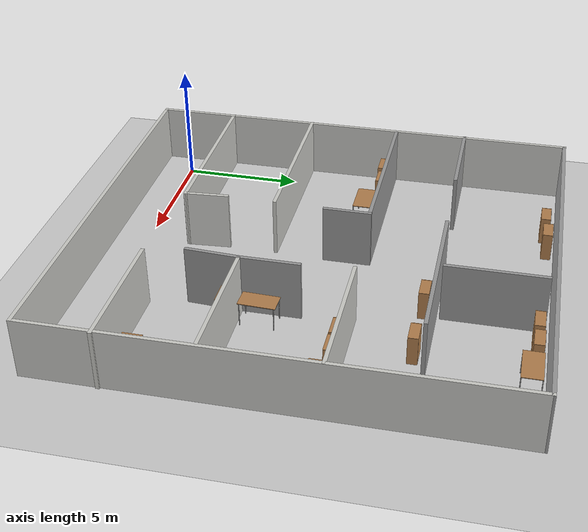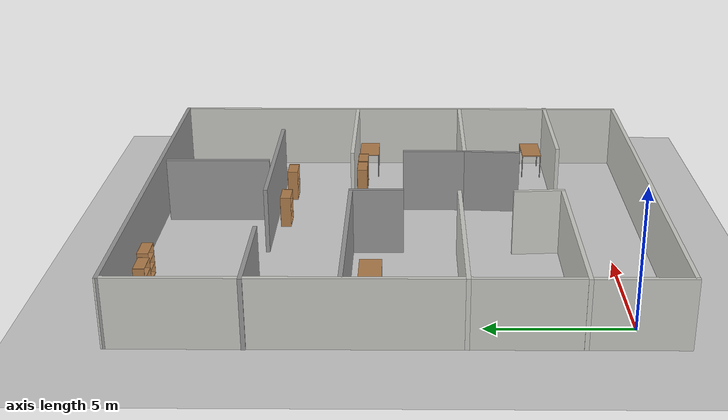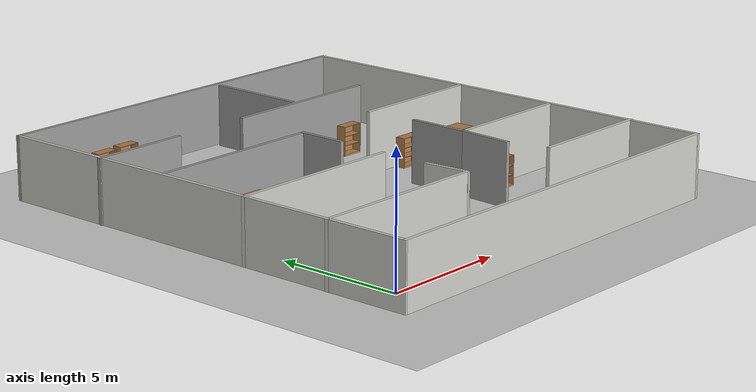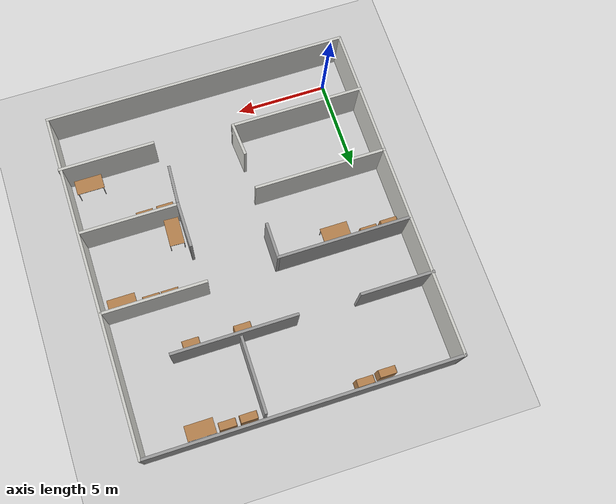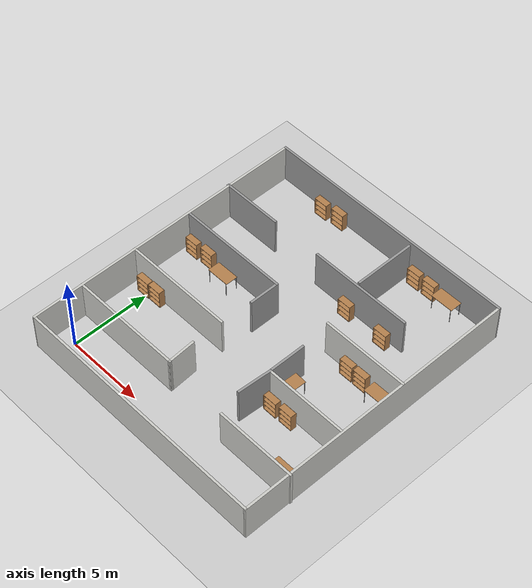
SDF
<sdf version="1.7">
 <world name="default">
  <light name="sun" type="directional">
   <pose>0 0 10 0 -0 0</pose>
   <diffuse>0.8 0.8 0.8 1</diffuse>
   <specular>0.2 0.2 0.2 1</specular>
   <attenuation>
    <range>1000</range>
    <constant>0.9</constant>
    <linear>0.01</linear>
    <quadratic>0.001</quadratic>
   </attenuation>
   <direction>-0.5 0.1 -0.9</direction>
   <spot><inner_angle>0</inner_angle><outer_angle>0</outer_angle><falloff>0</falloff></spot>
  </light>
  <model name="ground_plane">
   <static>1</static>
   <link name="link">
    <collision name="collision">
     <geometry><plane><normal>0 0 1</normal><size>100 100</size></plane></geometry>
     <surface><friction><ode><mu>100</mu><mu2>50</mu2></ode></friction></surface>
    </collision>
    <visual name="visual">
     <cast_shadows>0</cast_shadows>
     <geometry><plane><normal>0 0 1</normal><size>100 100</size></plane></geometry>
     <material>
      <script><uri>file://media/materials/scripts/gazebo.material</uri><name>Gazebo/Grey</name></script>
     </material>
    </visual>
   </link>
  </model>
  <gravity>0 0 -9.8</gravity>
  <magnetic_field>6e-06 2.3e-05 -4.2e-05</magnetic_field>
  <atmosphere type="adiabatic"/>
  <physics type="ode">
   <max_step_size>0.001</max_step_size>
   <real_time_factor>1</real_time_factor>
   <real_time_update_rate>1000</real_time_update_rate>
  </physics>
  <scene><ambient>0.4 0.4 0.4 1</ambient><background>0.7 0.7 0.7 1</background><shadows>1</shadows></scene>
  <spherical_coordinates>
   <surface_model>EARTH_WGS84</surface_model>
   <latitude_deg>0</latitude_deg>
   <longitude_deg>0</longitude_deg>
   <elevation>0</elevation>
   <heading_deg>0</heading_deg>
  </spherical_coordinates>
  <model name="ee_1">
   <pose>7.01305 7.77711 0 0 -0 0</pose>
   <link name="Wall_0">
    <collision name="Wall_0_Collision">
     <geometry><box><size>16.7607 0.15 2.5</size></box></geometry>
     <pose>0 0 1.25 0 -0 0</pose>
    </collision>
    <visual name="Wall_0_Visual">
     <pose>0 0 1.25 0 -0 0</pose>
     <geometry><box><size>16.7607 0.15 2.5</size></box></geometry>
     <material>
      <script><uri>file://media/materials/scripts/gazebo.material</uri><name>Gazebo/CeilingTiled</name></script>
      <ambient>0.921569 0.807843 0.615686 1</ambient>
     </material>
     <meta><layer>0</layer></meta>
    </visual>
    <pose>0.010352 -9.2685 0 0 -0 0</pose>
   </link>
   <link name="Wall_1">
    <collision name="Wall_1_Collision">
     <geometry><box><size>18.687 0.15 2.5</size></box></geometry>
     <pose>0 0 1.25 0 -0 0</pose>
    </collision>
    <visual name="Wall_1_Visual">
     <pose>0 0 1.25 0 -0 0</pose>
     <geometry><box><size>18.687 0.15 2.5</size></box></geometry>
     <material>
      <script><uri>file://media/materials/scripts/gazebo.material</uri><name>Gazebo/CeilingTiled</name></script>
      <ambient>0.921569 0.807843 0.615686 1</ambient>
     </material>
     <meta><layer>0</layer></meta>
    </visual>
    <pose>8.29685 0 0 0 -0 1.57285</pose>
   </link>
   <link name="Wall_2">
    <collision name="Wall_2_Collision">
     <geometry><box><size>16.761 0.15 2.5</size></box></geometry>
     <pose>0 0 1.25 0 -0 0</pose>
    </collision>
    <visual name="Wall_2_Visual">
     <pose>0 0 1.25 0 -0 0</pose>
     <geometry><box><size>16.761 0.15 2.5</size></box></geometry>
     <material>
      <script><uri>file://media/materials/scripts/gazebo.material</uri><name>Gazebo/Grey</name></script>
      <ambient>1 1 1 1</ambient>
     </material>
     <meta><layer>0</layer></meta>
    </visual>
    <pose>-0.027648 9.2685 0 0 -0 3.14159</pose>
   </link>
   <link name="Wall_21">
    <collision name="Wall_21_Collision">
     <geometry><box><size>7.373 0.15 2.5</size></box></geometry>
     <pose>0 0 1.25 0 -0 0</pose>
    </collision>
    <visual name="Wall_21_Visual">
     <pose>0 0 1.25 0 -0 0</pose>
     <geometry><box><size>7.373 0.15 2.5</size></box></geometry>
     <material>
      <script><uri>file://media/materials/scripts/gazebo.material</uri><name>Gazebo/CeilingTiled</name></script>
      <ambient>0.921569 0.807843 0.615686 1</ambient>
     </material>
     <meta><layer>0</layer></meta>
    </visual>
    <pose>-4.70665 -5.9765 0 0 -0 0</pose>
   </link>
   <link name="Wall_22">
    <collision name="Wall_22_Collision">
     <geometry><box><size>1.87777 0.15 2.5</size></box></geometry>
     <pose>0 0 1.25 0 -0 0</pose>
    </collision>
    <visual name="Wall_22_Visual">
     <pose>0 0 1.25 0 -0 0</pose>
     <geometry><box><size>1.87777 0.15 2.5</size></box></geometry>
     <material>
      <script><uri>file://media/materials/scripts/gazebo.material</uri><name>Gazebo/CeilingTiled</name></script>
      <ambient>0.921569 0.807843 0.615686 1</ambient>
     </material>
     <meta><layer>0</layer></meta>
    </visual>
    <pose>-1.15665 -5.115 0 0 -0 1.64206</pose>
   </link>
   <link name="Wall_24">
    <collision name="Wall_24_Collision">
     <geometry><box><size>7.25 0.15 2.5</size></box></geometry>
     <pose>0 0 1.25 0 -0 0</pose>
    </collision>
    <visual name="Wall_24_Visual">
     <pose>0 0 1.25 0 -0 0</pose>
     <geometry><box><size>7.25 0.15 2.5</size></box></geometry>
     <material>
      <script><uri>file://media/materials/scripts/gazebo.material</uri><name>Gazebo/CeilingTiled</name></script>
      <ambient>0.921569 0.807843 0.615686 1</ambient>
     </material>
     <meta><layer>0</layer></meta>
    </visual>
    <pose>-4.76815 -2.2145 0 0 -0 0</pose>
   </link>
   <link name="Wall_26">
    <collision name="Wall_26_Collision">
     <geometry><box><size>7.25 0.15 2.5</size></box></geometry>
     <pose>0 0 1.25 0 -0 0</pose>
    </collision>
    <visual name="Wall_26_Visual">
     <pose>0 0 1.25 0 -0 0</pose>
     <geometry><box><size>7.25 0.15 2.5</size></box></geometry>
     <material>
      <script><uri>file://media/materials/scripts/gazebo.material</uri><name>Gazebo/Grey</name></script>
      <ambient>1 1 1 1</ambient>
     </material>
     <meta><layer>0</layer></meta>
    </visual>
    <pose>-4.66117 1.74424 0 0 -0 0</pose>
   </link>
   <link name="Wall_27">
    <collision name="Wall_27_Collision">
     <geometry><box><size>2 0.15 2.5</size></box></geometry>
     <pose>0 0 1.25 0 -0 0</pose>
    </collision>
    <visual name="Wall_27_Visual">
     <pose>0 0 1.25 0 -0 0</pose>
     <geometry><box><size>2 0.15 2.5</size></box></geometry>
     <material>
      <script><uri>file://media/materials/scripts/gazebo.material</uri><name>Gazebo/Grey</name></script>
      <ambient>1 1 1 1</ambient>
     </material>
     <meta><layer>0</layer></meta>
    </visual>
    <pose>-1.11117 0.819242 0 0 -0 -1.5708</pose>
   </link>
   <link name="Wall_29">
    <collision name="Wall_29_Collision">
     <geometry><box><size>5.25 0.15 2.5</size></box></geometry>
     <pose>0 0 1.25 0 -0 0</pose>
    </collision>
    <visual name="Wall_29_Visual">
     <pose>0 0 1.25 0 -0 0</pose>
     <geometry><box><size>5.25 0.15 2.5</size></box></geometry>
     <material>
      <script><uri>file://media/materials/scripts/gazebo.material</uri><name>Gazebo/CeilingTiled</name></script>
      <ambient>0.921569 0.807843 0.615686 1</ambient>
     </material>
     <meta><layer>0</layer></meta>
    </visual>
    <pose>5.82485 -6.2815 0 0 -0 3.14159</pose>
   </link>
   <link name="Wall_3">
    <collision name="Wall_3_Collision">
     <geometry><box><size>18.687 0.15 2.5</size></box></geometry>
     <pose>0 0 1.25 0 -0 0</pose>
    </collision>
    <visual name="Wall_3_Visual">
     <pose>0 0 1.25 0 -0 0</pose>
     <geometry><box><size>18.687 0.15 2.5</size></box></geometry>
     <material>
      <script><uri>file://media/materials/scripts/gazebo.material</uri><name>Gazebo/CeilingTiled</name></script>
      <ambient>0.921569 0.807843 0.615686 1</ambient>
     </material>
     <meta><layer>0</layer></meta>
    </visual>
    <pose>-8.31415 0 0 0 -0 -1.56875</pose>
   </link>
   <link name="Wall_31">
    <collision name="Wall_31_Collision">
     <geometry><box><size>5.25 0.15 2.5</size></box></geometry>
     <pose>0 0 1.25 0 -0 0</pose>
    </collision>
    <visual name="Wall_31_Visual">
     <pose>0 0 1.25 0 -0 0</pose>
     <geometry><box><size>5.25 0.15 2.5</size></box></geometry>
     <material>
      <script><uri>file://media/materials/scripts/gazebo.material</uri><name>Gazebo/CeilingTiled</name></script>
      <ambient>0.921569 0.807843 0.615686 1</ambient>
     </material>
     <meta><layer>0</layer></meta>
    </visual>
    <pose>5.6268 -2.56856 0 0 -0 3.14159</pose>
   </link>
   <link name="Wall_32">
    <collision name="Wall_32_Collision">
     <geometry><box><size>2.257 0.15 2.5</size></box></geometry>
     <pose>0 0 1.25 0 -0 0</pose>
    </collision>
    <visual name="Wall_32_Visual">
     <pose>0 0 1.25 0 -0 0</pose>
     <geometry><box><size>2.257 0.15 2.5</size></box></geometry>
     <material>
      <script><uri>file://media/materials/scripts/gazebo.material</uri><name>Gazebo/Grey</name></script>
      <ambient>1 1 1 1</ambient>
     </material>
     <meta><layer>0</layer></meta>
    </visual>
    <pose>2.89214 -3.62025 0 0 -0 -1.62931</pose>
   </link>
   <link name="Wall_34">
    <collision name="Wall_34_Collision">
     <geometry><box><size>5.67802 0.15 2.5</size></box></geometry>
     <pose>0 0 1.25 0 -0 0</pose>
    </collision>
    <visual name="Wall_34_Visual">
     <pose>0 0 1.25 0 -0 0</pose>
     <geometry><box><size>5.67802 0.15 2.5</size></box></geometry>
     <material>
      <script><uri>file://media/materials/scripts/gazebo.material</uri><name>Gazebo/CeilingTiled</name></script>
      <ambient>0.921569 0.807843 0.615686 1</ambient>
     </material>
     <meta><layer>0</layer></meta>
    </visual>
    <pose>5.50385 1.8515 0 0 -0 3.14159</pose>
   </link>
   <link name="Wall_37">
    <collision name="Wall_37_Collision">
     <geometry><box><size>2.49661 0.15 2.5</size></box></geometry>
     <pose>0 0 1.25 0 -0 0</pose>
    </collision>
    <visual name="Wall_37_Visual">
     <pose>0 0 1.25 0 -0 0</pose>
     <geometry><box><size>2.49661 0.15 2.5</size></box></geometry>
     <material>
      <script><uri>file://media/materials/scripts/gazebo.material</uri><name>Gazebo/Grey</name></script>
      <ambient>1 1 1 1</ambient>
     </material>
     <meta><layer>0</layer></meta>
    </visual>
    <pose>2.95366 -1.39525 0 0 -0 1.57086</pose>
   </link>
   <link name="Wall_39">
    <collision name="Wall_39_Collision">
     <geometry><box><size>4 0.15 2.5</size></box></geometry>
     <pose>0 0 1.25 0 -0 0</pose>
    </collision>
    <visual name="Wall_39_Visual">
     <pose>0 0 1.25 0 -0 0</pose>
     <geometry><box><size>4 0.15 2.5</size></box></geometry>
     <material>
      <script><uri>file://media/materials/scripts/gazebo.material</uri><name>Gazebo/Grey</name></script>
      <ambient>1 1 1 1</ambient>
     </material>
     <meta><layer>0</layer></meta>
    </visual>
    <pose>-6.44985 4.83089 0 0 -0 3.14159</pose>
   </link>
   <link name="Wall_44">
    <collision name="Wall_44_Collision">
     <geometry><box><size>6.75 0.15 2.5</size></box></geometry>
     <pose>0 0 1.25 0 -0 0</pose>
    </collision>
    <visual name="Wall_44_Visual">
     <pose>0 0 1.25 0 -0 0</pose>
     <geometry><box><size>6.75 0.15 2.5</size></box></geometry>
     <material>
      <script><uri>file://media/materials/scripts/gazebo.material</uri><name>Gazebo/Grey</name></script>
      <ambient>1 1 1 1</ambient>
     </material>
     <meta><layer>0</layer></meta>
    </visual>
    <pose>2.17764 4.84934 0 0 -0 0</pose>
   </link>
   <link name="Wall_48">
    <collision name="Wall_48_Collision">
     <geometry><box><size>4 0.15 2.5</size></box></geometry>
     <pose>0 0 1.25 0 -0 0</pose>
    </collision>
    <visual name="Wall_48_Visual">
     <pose>0 0 1.25 0 -0 0</pose>
     <geometry><box><size>4 0.15 2.5</size></box></geometry>
     <material>
      <script><uri>file://media/materials/scripts/gazebo.material</uri><name>Gazebo/Grey</name></script>
      <ambient>1 1 1 1</ambient>
     </material>
     <meta><layer>0</layer></meta>
    </visual>
    <pose>1.88593 7.03139 0 0 -0 1.5708</pose>
   </link>
   <static>1</static>
  </model>
  <model name="bookshelf">
   <static>1</static>
   <link name="link">
    <inertial><mass>1</mass></inertial>
    <collision name="back">
     <pose>0 0.005 0.6 0 -0 0</pose>
     <geometry><box><size>0.9 0.01 1.2</size></box></geometry>
    </collision>
    <visual name="visual1">
     <pose>0 0.005 0.6 0 -0 0</pose>
     <geometry><box><size>0.9 0.01 1.2</size></box></geometry>
     <material>
      <script><uri>file://media/materials/scripts/gazebo.material</uri><name>Gazebo/Wood</name></script>
     </material>
    </visual>
    <collision name="left_side">
     <pose>0.45 -0.195 0.6 0 -0 0</pose>
     <geometry><box><size>0.02 0.4 1.2</size></box></geometry>
    </collision>
    <visual name="visual2">
     <pose>0.45 -0.195 0.6 0 -0 0</pose>
     <geometry><box><size>0.02 0.4 1.2</size></box></geometry>
     <material>
      <script><uri>file://media/materials/scripts/gazebo.material</uri><name>Gazebo/Wood</name></script>
     </material>
    </visual>
    <collision name="right_side">
     <pose>-0.45 -0.195 0.6 0 -0 0</pose>
     <geometry><box><size>0.02 0.4 1.2</size></box></geometry>
    </collision>
    <visual name="visual3">
     <pose>-0.45 -0.195 0.6 0 -0 0</pose>
     <geometry><box><size>0.02 0.4 1.2</size></box></geometry>
     <material>
      <script><uri>file://media/materials/scripts/gazebo.material</uri><name>Gazebo/Wood</name></script>
     </material>
    </visual>
    <collision name="bottom">
     <pose>0 -0.195 0.03 0 -0 0</pose>
     <geometry><box><size>0.88 0.4 0.06</size></box></geometry>
    </collision>
    <visual name="visual4">
     <pose>0 -0.195 0.03 0 -0 0</pose>
     <geometry><box><size>0.88 0.4 0.06</size></box></geometry>
     <material>
      <script><uri>file://media/materials/scripts/gazebo.material</uri><name>Gazebo/Wood</name></script>
     </material>
    </visual>
    <collision name="top">
     <pose>0 -0.195 1.19 0 -0 0</pose>
     <geometry><box><size>0.88 0.4 0.02</size></box></geometry>
    </collision>
    <visual name="visual5">
     <pose>0 -0.195 1.19 0 -0 0</pose>
     <geometry><box><size>0.88 0.4 0.02</size></box></geometry>
     <material>
      <script><uri>file://media/materials/scripts/gazebo.material</uri><name>Gazebo/Wood</name></script>
     </material>
    </visual>
    <collision name="low_shelf">
     <pose>0 -0.195 0.43 0 -0 0</pose>
     <geometry><box><size>0.88 0.4 0.02</size></box></geometry>
    </collision>
    <visual name="visual6">
     <pose>0 -0.195 0.43 0 -0 0</pose>
     <geometry><box><size>0.88 0.4 0.02</size></box></geometry>
     <material>
      <script><uri>file://media/materials/scripts/gazebo.material</uri><name>Gazebo/Wood</name></script>
     </material>
    </visual>
    <collision name="high_shelf">
     <pose>0 -0.195 0.8 0 -0 0</pose>
     <geometry><box><size>0.88 0.4 0.02</size></box></geometry>
    </collision>
    <visual name="visual7">
     <pose>0 -0.195 0.8 0 -0 0</pose>
     <geometry><box><size>0.88 0.4 0.02</size></box></geometry>
     <material>
      <script><uri>file://media/materials/scripts/gazebo.material</uri><name>Gazebo/Wood</name></script>
     </material>
    </visual>
   </link>
   <pose>8.64014 12.3736 0 0 -0 0</pose>
  </model>
  <model name="bookshelf_0">
   <static>1</static>
   <link name="link">
    <inertial><mass>1</mass></inertial>
    <collision name="back">
     <pose>0 0.005 0.6 0 -0 0</pose>
     <geometry><box><size>0.9 0.01 1.2</size></box></geometry>
    </collision>
    <visual name="visual1">
     <pose>0 0.005 0.6 0 -0 0</pose>
     <geometry><box><size>0.9 0.01 1.2</size></box></geometry>
     <material>
      <script><uri>file://media/materials/scripts/gazebo.material</uri><name>Gazebo/Wood</name></script>
     </material>
    </visual>
    <collision name="left_side">
     <pose>0.45 -0.195 0.6 0 -0 0</pose>
     <geometry><box><size>0.02 0.4 1.2</size></box></geometry>
    </collision>
    <visual name="visual2">
     <pose>0.45 -0.195 0.6 0 -0 0</pose>
     <geometry><box><size>0.02 0.4 1.2</size></box></geometry>
     <material>
      <script><uri>file://media/materials/scripts/gazebo.material</uri><name>Gazebo/Wood</name></script>
     </material>
    </visual>
    <collision name="right_side">
     <pose>-0.45 -0.195 0.6 0 -0 0</pose>
     <geometry><box><size>0.02 0.4 1.2</size></box></geometry>
    </collision>
    <visual name="visual3">
     <pose>-0.45 -0.195 0.6 0 -0 0</pose>
     <geometry><box><size>0.02 0.4 1.2</size></box></geometry>
     <material>
      <script><uri>file://media/materials/scripts/gazebo.material</uri><name>Gazebo/Wood</name></script>
     </material>
    </visual>
    <collision name="bottom">
     <pose>0 -0.195 0.03 0 -0 0</pose>
     <geometry><box><size>0.88 0.4 0.06</size></box></geometry>
    </collision>
    <visual name="visual4">
     <pose>0 -0.195 0.03 0 -0 0</pose>
     <geometry><box><size>0.88 0.4 0.06</size></box></geometry>
     <material>
      <script><uri>file://media/materials/scripts/gazebo.material</uri><name>Gazebo/Wood</name></script>
     </material>
    </visual>
    <collision name="top">
     <pose>0 -0.195 1.19 0 -0 0</pose>
     <geometry><box><size>0.88 0.4 0.02</size></box></geometry>
    </collision>
    <visual name="visual5">
     <pose>0 -0.195 1.19 0 -0 0</pose>
     <geometry><box><size>0.88 0.4 0.02</size></box></geometry>
     <material>
      <script><uri>file://media/materials/scripts/gazebo.material</uri><name>Gazebo/Wood</name></script>
     </material>
    </visual>
    <collision name="low_shelf">
     <pose>0 -0.195 0.43 0 -0 0</pose>
     <geometry><box><size>0.88 0.4 0.02</size></box></geometry>
    </collision>
    <visual name="visual6">
     <pose>0 -0.195 0.43 0 -0 0</pose>
     <geometry><box><size>0.88 0.4 0.02</size></box></geometry>
     <material>
      <script><uri>file://media/materials/scripts/gazebo.material</uri><name>Gazebo/Wood</name></script>
     </material>
    </visual>
    <collision name="high_shelf">
     <pose>0 -0.195 0.8 0 -0 0</pose>
     <geometry><box><size>0.88 0.4 0.02</size></box></geometry>
    </collision>
    <visual name="visual7">
     <pose>0 -0.195 0.8 0 -0 0</pose>
     <geometry><box><size>0.88 0.4 0.02</size></box></geometry>
     <material>
      <script><uri>file://media/materials/scripts/gazebo.material</uri><name>Gazebo/Wood</name></script>
     </material>
    </visual>
   </link>
   <pose>11.3913 12.3426 0 0 -0 0</pose>
  </model>
  <model name="bookshelf_1">
   <static>1</static>
   <link name="link">
    <inertial><mass>1</mass></inertial>
    <collision name="back">
     <pose>0 0.005 0.6 0 -0 0</pose>
     <geometry><box><size>0.9 0.01 1.2</size></box></geometry>
    </collision>
    <visual name="visual1">
     <pose>0 0.005 0.6 0 -0 0</pose>
     <geometry><box><size>0.9 0.01 1.2</size></box></geometry>
     <material>
      <script><uri>file://media/materials/scripts/gazebo.material</uri><name>Gazebo/Wood</name></script>
     </material>
    </visual>
    <collision name="left_side">
     <pose>0.45 -0.195 0.6 0 -0 0</pose>
     <geometry><box><size>0.02 0.4 1.2</size></box></geometry>
    </collision>
    <visual name="visual2">
     <pose>0.45 -0.195 0.6 0 -0 0</pose>
     <geometry><box><size>0.02 0.4 1.2</size></box></geometry>
     <material>
      <script><uri>file://media/materials/scripts/gazebo.material</uri><name>Gazebo/Wood</name></script>
     </material>
    </visual>
    <collision name="right_side">
     <pose>-0.45 -0.195 0.6 0 -0 0</pose>
     <geometry><box><size>0.02 0.4 1.2</size></box></geometry>
    </collision>
    <visual name="visual3">
     <pose>-0.45 -0.195 0.6 0 -0 0</pose>
     <geometry><box><size>0.02 0.4 1.2</size></box></geometry>
     <material>
      <script><uri>file://media/materials/scripts/gazebo.material</uri><name>Gazebo/Wood</name></script>
     </material>
    </visual>
    <collision name="bottom">
     <pose>0 -0.195 0.03 0 -0 0</pose>
     <geometry><box><size>0.88 0.4 0.06</size></box></geometry>
    </collision>
    <visual name="visual4">
     <pose>0 -0.195 0.03 0 -0 0</pose>
     <geometry><box><size>0.88 0.4 0.06</size></box></geometry>
     <material>
      <script><uri>file://media/materials/scripts/gazebo.material</uri><name>Gazebo/Wood</name></script>
     </material>
    </visual>
    <collision name="top">
     <pose>0 -0.195 1.19 0 -0 0</pose>
     <geometry><box><size>0.88 0.4 0.02</size></box></geometry>
    </collision>
    <visual name="visual5">
     <pose>0 -0.195 1.19 0 -0 0</pose>
     <geometry><box><size>0.88 0.4 0.02</size></box></geometry>
     <material>
      <script><uri>file://media/materials/scripts/gazebo.material</uri><name>Gazebo/Wood</name></script>
     </material>
    </visual>
    <collision name="low_shelf">
     <pose>0 -0.195 0.43 0 -0 0</pose>
     <geometry><box><size>0.88 0.4 0.02</size></box></geometry>
    </collision>
    <visual name="visual6">
     <pose>0 -0.195 0.43 0 -0 0</pose>
     <geometry><box><size>0.88 0.4 0.02</size></box></geometry>
     <material>
      <script><uri>file://media/materials/scripts/gazebo.material</uri><name>Gazebo/Wood</name></script>
     </material>
    </visual>
    <collision name="high_shelf">
     <pose>0 -0.195 0.8 0 -0 0</pose>
     <geometry><box><size>0.88 0.4 0.02</size></box></geometry>
    </collision>
    <visual name="visual7">
     <pose>0 -0.195 0.8 0 -0 0</pose>
     <geometry><box><size>0.88 0.4 0.02</size></box></geometry>
     <material>
      <script><uri>file://media/materials/scripts/gazebo.material</uri><name>Gazebo/Wood</name></script>
     </material>
    </visual>
   </link>
   <pose>0.748044 5.44462 0 0 -0 0</pose>
  </model>
  <model name="bookshelf_2">
   <static>1</static>
   <link name="link">
    <inertial><mass>1</mass></inertial>
    <collision name="back">
     <pose>0 0.005 0.6 0 -0 0</pose>
     <geometry><box><size>0.9 0.01 1.2</size></box></geometry>
    </collision>
    <visual name="visual1">
     <pose>0 0.005 0.6 0 -0 0</pose>
     <geometry><box><size>0.9 0.01 1.2</size></box></geometry>
     <material>
      <script><uri>file://media/materials/scripts/gazebo.material</uri><name>Gazebo/Wood</name></script>
     </material>
    </visual>
    <collision name="left_side">
     <pose>0.45 -0.195 0.6 0 -0 0</pose>
     <geometry><box><size>0.02 0.4 1.2</size></box></geometry>
    </collision>
    <visual name="visual2">
     <pose>0.45 -0.195 0.6 0 -0 0</pose>
     <geometry><box><size>0.02 0.4 1.2</size></box></geometry>
     <material>
      <script><uri>file://media/materials/scripts/gazebo.material</uri><name>Gazebo/Wood</name></script>
     </material>
    </visual>
    <collision name="right_side">
     <pose>-0.45 -0.195 0.6 0 -0 0</pose>
     <geometry><box><size>0.02 0.4 1.2</size></box></geometry>
    </collision>
    <visual name="visual3">
     <pose>-0.45 -0.195 0.6 0 -0 0</pose>
     <geometry><box><size>0.02 0.4 1.2</size></box></geometry>
     <material>
      <script><uri>file://media/materials/scripts/gazebo.material</uri><name>Gazebo/Wood</name></script>
     </material>
    </visual>
    <collision name="bottom">
     <pose>0 -0.195 0.03 0 -0 0</pose>
     <geometry><box><size>0.88 0.4 0.06</size></box></geometry>
    </collision>
    <visual name="visual4">
     <pose>0 -0.195 0.03 0 -0 0</pose>
     <geometry><box><size>0.88 0.4 0.06</size></box></geometry>
     <material>
      <script><uri>file://media/materials/scripts/gazebo.material</uri><name>Gazebo/Wood</name></script>
     </material>
    </visual>
    <collision name="top">
     <pose>0 -0.195 1.19 0 -0 0</pose>
     <geometry><box><size>0.88 0.4 0.02</size></box></geometry>
    </collision>
    <visual name="visual5">
     <pose>0 -0.195 1.19 0 -0 0</pose>
     <geometry><box><size>0.88 0.4 0.02</size></box></geometry>
     <material>
      <script><uri>file://media/materials/scripts/gazebo.material</uri><name>Gazebo/Wood</name></script>
     </material>
    </visual>
    <collision name="low_shelf">
     <pose>0 -0.195 0.43 0 -0 0</pose>
     <geometry><box><size>0.88 0.4 0.02</size></box></geometry>
    </collision>
    <visual name="visual6">
     <pose>0 -0.195 0.43 0 -0 0</pose>
     <geometry><box><size>0.88 0.4 0.02</size></box></geometry>
     <material>
      <script><uri>file://media/materials/scripts/gazebo.material</uri><name>Gazebo/Wood</name></script>
     </material>
    </visual>
    <collision name="high_shelf">
     <pose>0 -0.195 0.8 0 -0 0</pose>
     <geometry><box><size>0.88 0.4 0.02</size></box></geometry>
    </collision>
    <visual name="visual7">
     <pose>0 -0.195 0.8 0 -0 0</pose>
     <geometry><box><size>0.88 0.4 0.02</size></box></geometry>
     <material>
      <script><uri>file://media/materials/scripts/gazebo.material</uri><name>Gazebo/Wood</name></script>
     </material>
    </visual>
   </link>
   <pose>3.57686 16.847 0 0 -0 0</pose>
  </model>
  <model name="bookshelf_3">
   <static>1</static>
   <link name="link">
    <inertial><mass>1</mass></inertial>
    <collision name="back">
     <pose>0 0.005 0.6 0 -0 0</pose>
     <geometry><box><size>0.9 0.01 1.2</size></box></geometry>
    </collision>
    <visual name="visual1">
     <pose>0 0.005 0.6 0 -0 0</pose>
     <geometry><box><size>0.9 0.01 1.2</size></box></geometry>
     <material>
      <script><uri>file://media/materials/scripts/gazebo.material</uri><name>Gazebo/Wood</name></script>
     </material>
    </visual>
    <collision name="left_side">
     <pose>0.45 -0.195 0.6 0 -0 0</pose>
     <geometry><box><size>0.02 0.4 1.2</size></box></geometry>
    </collision>
    <visual name="visual2">
     <pose>0.45 -0.195 0.6 0 -0 0</pose>
     <geometry><box><size>0.02 0.4 1.2</size></box></geometry>
     <material>
      <script><uri>file://media/materials/scripts/gazebo.material</uri><name>Gazebo/Wood</name></script>
     </material>
    </visual>
    <collision name="right_side">
     <pose>-0.45 -0.195 0.6 0 -0 0</pose>
     <geometry><box><size>0.02 0.4 1.2</size></box></geometry>
    </collision>
    <visual name="visual3">
     <pose>-0.45 -0.195 0.6 0 -0 0</pose>
     <geometry><box><size>0.02 0.4 1.2</size></box></geometry>
     <material>
      <script><uri>file://media/materials/scripts/gazebo.material</uri><name>Gazebo/Wood</name></script>
     </material>
    </visual>
    <collision name="bottom">
     <pose>0 -0.195 0.03 0 -0 0</pose>
     <geometry><box><size>0.88 0.4 0.06</size></box></geometry>
    </collision>
    <visual name="visual4">
     <pose>0 -0.195 0.03 0 -0 0</pose>
     <geometry><box><size>0.88 0.4 0.06</size></box></geometry>
     <material>
      <script><uri>file://media/materials/scripts/gazebo.material</uri><name>Gazebo/Wood</name></script>
     </material>
    </visual>
    <collision name="top">
     <pose>0 -0.195 1.19 0 -0 0</pose>
     <geometry><box><size>0.88 0.4 0.02</size></box></geometry>
    </collision>
    <visual name="visual5">
     <pose>0 -0.195 1.19 0 -0 0</pose>
     <geometry><box><size>0.88 0.4 0.02</size></box></geometry>
     <material>
      <script><uri>file://media/materials/scripts/gazebo.material</uri><name>Gazebo/Wood</name></script>
     </material>
    </visual>
    <collision name="low_shelf">
     <pose>0 -0.195 0.43 0 -0 0</pose>
     <geometry><box><size>0.88 0.4 0.02</size></box></geometry>
    </collision>
    <visual name="visual6">
     <pose>0 -0.195 0.43 0 -0 0</pose>
     <geometry><box><size>0.88 0.4 0.02</size></box></geometry>
     <material>
      <script><uri>file://media/materials/scripts/gazebo.material</uri><name>Gazebo/Wood</name></script>
     </material>
    </visual>
    <collision name="high_shelf">
     <pose>0 -0.195 0.8 0 -0 0</pose>
     <geometry><box><size>0.88 0.4 0.02</size></box></geometry>
    </collision>
    <visual name="visual7">
     <pose>0 -0.195 0.8 0 -0 0</pose>
     <geometry><box><size>0.88 0.4 0.02</size></box></geometry>
     <material>
      <script><uri>file://media/materials/scripts/gazebo.material</uri><name>Gazebo/Wood</name></script>
     </material>
    </visual>
   </link>
   <pose>2.35825 16.7303 0 0 -0 0</pose>
  </model>
  <model name="bookshelf_4">
   <static>1</static>
   <link name="link">
    <inertial><mass>1</mass></inertial>
    <collision name="back">
     <pose>0 0.005 0.6 0 -0 0</pose>
     <geometry><box><size>0.9 0.01 1.2</size></box></geometry>
    </collision>
    <visual name="visual1">
     <pose>0 0.005 0.6 0 -0 0</pose>
     <geometry><box><size>0.9 0.01 1.2</size></box></geometry>
     <material>
      <script><uri>file://media/materials/scripts/gazebo.material</uri><name>Gazebo/Wood</name></script>
     </material>
    </visual>
    <collision name="left_side">
     <pose>0.45 -0.195 0.6 0 -0 0</pose>
     <geometry><box><size>0.02 0.4 1.2</size></box></geometry>
    </collision>
    <visual name="visual2">
     <pose>0.45 -0.195 0.6 0 -0 0</pose>
     <geometry><box><size>0.02 0.4 1.2</size></box></geometry>
     <material>
      <script><uri>file://media/materials/scripts/gazebo.material</uri><name>Gazebo/Wood</name></script>
     </material>
    </visual>
    <collision name="right_side">
     <pose>-0.45 -0.195 0.6 0 -0 0</pose>
     <geometry><box><size>0.02 0.4 1.2</size></box></geometry>
    </collision>
    <visual name="visual3">
     <pose>-0.45 -0.195 0.6 0 -0 0</pose>
     <geometry><box><size>0.02 0.4 1.2</size></box></geometry>
     <material>
      <script><uri>file://media/materials/scripts/gazebo.material</uri><name>Gazebo/Wood</name></script>
     </material>
    </visual>
    <collision name="bottom">
     <pose>0 -0.195 0.03 0 -0 0</pose>
     <geometry><box><size>0.88 0.4 0.06</size></box></geometry>
    </collision>
    <visual name="visual4">
     <pose>0 -0.195 0.03 0 -0 0</pose>
     <geometry><box><size>0.88 0.4 0.06</size></box></geometry>
     <material>
      <script><uri>file://media/materials/scripts/gazebo.material</uri><name>Gazebo/Wood</name></script>
     </material>
    </visual>
    <collision name="top">
     <pose>0 -0.195 1.19 0 -0 0</pose>
     <geometry><box><size>0.88 0.4 0.02</size></box></geometry>
    </collision>
    <visual name="visual5">
     <pose>0 -0.195 1.19 0 -0 0</pose>
     <geometry><box><size>0.88 0.4 0.02</size></box></geometry>
     <material>
      <script><uri>file://media/materials/scripts/gazebo.material</uri><name>Gazebo/Wood</name></script>
     </material>
    </visual>
    <collision name="low_shelf">
     <pose>0 -0.195 0.43 0 -0 0</pose>
     <geometry><box><size>0.88 0.4 0.02</size></box></geometry>
    </collision>
    <visual name="visual6">
     <pose>0 -0.195 0.43 0 -0 0</pose>
     <geometry><box><size>0.88 0.4 0.02</size></box></geometry>
     <material>
      <script><uri>file://media/materials/scripts/gazebo.material</uri><name>Gazebo/Wood</name></script>
     </material>
    </visual>
    <collision name="high_shelf">
     <pose>0 -0.195 0.8 0 -0 0</pose>
     <geometry><box><size>0.88 0.4 0.02</size></box></geometry>
    </collision>
    <visual name="visual7">
     <pose>0 -0.195 0.8 0 -0 0</pose>
     <geometry><box><size>0.88 0.4 0.02</size></box></geometry>
     <material>
      <script><uri>file://media/materials/scripts/gazebo.material</uri><name>Gazebo/Wood</name></script>
     </material>
    </visual>
   </link>
   <pose>-0.497717 9.2956 0 0 -0 0</pose>
  </model>
  <model name="bookshelf_5">
   <static>1</static>
   <link name="link">
    <inertial><mass>1</mass></inertial>
    <collision name="back">
     <pose>0 0.005 0.6 0 -0 0</pose>
     <geometry><box><size>0.9 0.01 1.2</size></box></geometry>
    </collision>
    <visual name="visual1">
     <pose>0 0.005 0.6 0 -0 0</pose>
     <geometry><box><size>0.9 0.01 1.2</size></box></geometry>
     <material>
      <script><uri>file://media/materials/scripts/gazebo.material</uri><name>Gazebo/Wood</name></script>
     </material>
    </visual>
    <collision name="left_side">
     <pose>0.45 -0.195 0.6 0 -0 0</pose>
     <geometry><box><size>0.02 0.4 1.2</size></box></geometry>
    </collision>
    <visual name="visual2">
     <pose>0.45 -0.195 0.6 0 -0 0</pose>
     <geometry><box><size>0.02 0.4 1.2</size></box></geometry>
     <material>
      <script><uri>file://media/materials/scripts/gazebo.material</uri><name>Gazebo/Wood</name></script>
     </material>
    </visual>
    <collision name="right_side">
     <pose>-0.45 -0.195 0.6 0 -0 0</pose>
     <geometry><box><size>0.02 0.4 1.2</size></box></geometry>
    </collision>
    <visual name="visual3">
     <pose>-0.45 -0.195 0.6 0 -0 0</pose>
     <geometry><box><size>0.02 0.4 1.2</size></box></geometry>
     <material>
      <script><uri>file://media/materials/scripts/gazebo.material</uri><name>Gazebo/Wood</name></script>
     </material>
    </visual>
    <collision name="bottom">
     <pose>0 -0.195 0.03 0 -0 0</pose>
     <geometry><box><size>0.88 0.4 0.06</size></box></geometry>
    </collision>
    <visual name="visual4">
     <pose>0 -0.195 0.03 0 -0 0</pose>
     <geometry><box><size>0.88 0.4 0.06</size></box></geometry>
     <material>
      <script><uri>file://media/materials/scripts/gazebo.material</uri><name>Gazebo/Wood</name></script>
     </material>
    </visual>
    <collision name="top">
     <pose>0 -0.195 1.19 0 -0 0</pose>
     <geometry><box><size>0.88 0.4 0.02</size></box></geometry>
    </collision>
    <visual name="visual5">
     <pose>0 -0.195 1.19 0 -0 0</pose>
     <geometry><box><size>0.88 0.4 0.02</size></box></geometry>
     <material>
      <script><uri>file://media/materials/scripts/gazebo.material</uri><name>Gazebo/Wood</name></script>
     </material>
    </visual>
    <collision name="low_shelf">
     <pose>0 -0.195 0.43 0 -0 0</pose>
     <geometry><box><size>0.88 0.4 0.02</size></box></geometry>
    </collision>
    <visual name="visual6">
     <pose>0 -0.195 0.43 0 -0 0</pose>
     <geometry><box><size>0.88 0.4 0.02</size></box></geometry>
     <material>
      <script><uri>file://media/materials/scripts/gazebo.material</uri><name>Gazebo/Wood</name></script>
     </material>
    </visual>
    <collision name="high_shelf">
     <pose>0 -0.195 0.8 0 -0 0</pose>
     <geometry><box><size>0.88 0.4 0.02</size></box></geometry>
    </collision>
    <visual name="visual7">
     <pose>0 -0.195 0.8 0 -0 0</pose>
     <geometry><box><size>0.88 0.4 0.02</size></box></geometry>
     <material>
      <script><uri>file://media/materials/scripts/gazebo.material</uri><name>Gazebo/Wood</name></script>
     </material>
    </visual>
   </link>
   <pose>0.662005 9.36987 0 0 -0 0</pose>
  </model>
  <model name="bookshelf_6">
   <static>1</static>
   <link name="link">
    <inertial><mass>1</mass></inertial>
    <collision name="back">
     <pose>0 0.005 0.6 0 -0 0</pose>
     <geometry><box><size>0.9 0.01 1.2</size></box></geometry>
    </collision>
    <visual name="visual1">
     <pose>0 0.005 0.6 0 -0 0</pose>
     <geometry><box><size>0.9 0.01 1.2</size></box></geometry>
     <material>
      <script><uri>file://media/materials/scripts/gazebo.material</uri><name>Gazebo/Wood</name></script>
     </material>
    </visual>
    <collision name="left_side">
     <pose>0.45 -0.195 0.6 0 -0 0</pose>
     <geometry><box><size>0.02 0.4 1.2</size></box></geometry>
    </collision>
    <visual name="visual2">
     <pose>0.45 -0.195 0.6 0 -0 0</pose>
     <geometry><box><size>0.02 0.4 1.2</size></box></geometry>
     <material>
      <script><uri>file://media/materials/scripts/gazebo.material</uri><name>Gazebo/Wood</name></script>
     </material>
    </visual>
    <collision name="right_side">
     <pose>-0.45 -0.195 0.6 0 -0 0</pose>
     <geometry><box><size>0.02 0.4 1.2</size></box></geometry>
    </collision>
    <visual name="visual3">
     <pose>-0.45 -0.195 0.6 0 -0 0</pose>
     <geometry><box><size>0.02 0.4 1.2</size></box></geometry>
     <material>
      <script><uri>file://media/materials/scripts/gazebo.material</uri><name>Gazebo/Wood</name></script>
     </material>
    </visual>
    <collision name="bottom">
     <pose>0 -0.195 0.03 0 -0 0</pose>
     <geometry><box><size>0.88 0.4 0.06</size></box></geometry>
    </collision>
    <visual name="visual4">
     <pose>0 -0.195 0.03 0 -0 0</pose>
     <geometry><box><size>0.88 0.4 0.06</size></box></geometry>
     <material>
      <script><uri>file://media/materials/scripts/gazebo.material</uri><name>Gazebo/Wood</name></script>
     </material>
    </visual>
    <collision name="top">
     <pose>0 -0.195 1.19 0 -0 0</pose>
     <geometry><box><size>0.88 0.4 0.02</size></box></geometry>
    </collision>
    <visual name="visual5">
     <pose>0 -0.195 1.19 0 -0 0</pose>
     <geometry><box><size>0.88 0.4 0.02</size></box></geometry>
     <material>
      <script><uri>file://media/materials/scripts/gazebo.material</uri><name>Gazebo/Wood</name></script>
     </material>
    </visual>
    <collision name="low_shelf">
     <pose>0 -0.195 0.43 0 -0 0</pose>
     <geometry><box><size>0.88 0.4 0.02</size></box></geometry>
    </collision>
    <visual name="visual6">
     <pose>0 -0.195 0.43 0 -0 0</pose>
     <geometry><box><size>0.88 0.4 0.02</size></box></geometry>
     <material>
      <script><uri>file://media/materials/scripts/gazebo.material</uri><name>Gazebo/Wood</name></script>
     </material>
    </visual>
    <collision name="high_shelf">
     <pose>0 -0.195 0.8 0 -0 0</pose>
     <geometry><box><size>0.88 0.4 0.02</size></box></geometry>
    </collision>
    <visual name="visual7">
     <pose>0 -0.195 0.8 0 -0 0</pose>
     <geometry><box><size>0.88 0.4 0.02</size></box></geometry>
     <material>
      <script><uri>file://media/materials/scripts/gazebo.material</uri><name>Gazebo/Wood</name></script>
     </material>
    </visual>
   </link>
   <pose>11.6676 9.51183 0 0 -0 0</pose>
  </model>
  <model name="bookshelf_7">
   <static>1</static>
   <link name="link">
    <inertial><mass>1</mass></inertial>
    <collision name="back">
     <pose>0 0.005 0.6 0 -0 0</pose>
     <geometry><box><size>0.9 0.01 1.2</size></box></geometry>
    </collision>
    <visual name="visual1">
     <pose>0 0.005 0.6 0 -0 0</pose>
     <geometry><box><size>0.9 0.01 1.2</size></box></geometry>
     <material>
      <script><uri>file://media/materials/scripts/gazebo.material</uri><name>Gazebo/Wood</name></script>
     </material>
    </visual>
    <collision name="left_side">
     <pose>0.45 -0.195 0.6 0 -0 0</pose>
     <geometry><box><size>0.02 0.4 1.2</size></box></geometry>
    </collision>
    <visual name="visual2">
     <pose>0.45 -0.195 0.6 0 -0 0</pose>
     <geometry><box><size>0.02 0.4 1.2</size></box></geometry>
     <material>
      <script><uri>file://media/materials/scripts/gazebo.material</uri><name>Gazebo/Wood</name></script>
     </material>
    </visual>
    <collision name="right_side">
     <pose>-0.45 -0.195 0.6 0 -0 0</pose>
     <geometry><box><size>0.02 0.4 1.2</size></box></geometry>
    </collision>
    <visual name="visual3">
     <pose>-0.45 -0.195 0.6 0 -0 0</pose>
     <geometry><box><size>0.02 0.4 1.2</size></box></geometry>
     <material>
      <script><uri>file://media/materials/scripts/gazebo.material</uri><name>Gazebo/Wood</name></script>
     </material>
    </visual>
    <collision name="bottom">
     <pose>0 -0.195 0.03 0 -0 0</pose>
     <geometry><box><size>0.88 0.4 0.06</size></box></geometry>
    </collision>
    <visual name="visual4">
     <pose>0 -0.195 0.03 0 -0 0</pose>
     <geometry><box><size>0.88 0.4 0.06</size></box></geometry>
     <material>
      <script><uri>file://media/materials/scripts/gazebo.material</uri><name>Gazebo/Wood</name></script>
     </material>
    </visual>
    <collision name="top">
     <pose>0 -0.195 1.19 0 -0 0</pose>
     <geometry><box><size>0.88 0.4 0.02</size></box></geometry>
    </collision>
    <visual name="visual5">
     <pose>0 -0.195 1.19 0 -0 0</pose>
     <geometry><box><size>0.88 0.4 0.02</size></box></geometry>
     <material>
      <script><uri>file://media/materials/scripts/gazebo.material</uri><name>Gazebo/Wood</name></script>
     </material>
    </visual>
    <collision name="low_shelf">
     <pose>0 -0.195 0.43 0 -0 0</pose>
     <geometry><box><size>0.88 0.4 0.02</size></box></geometry>
    </collision>
    <visual name="visual6">
     <pose>0 -0.195 0.43 0 -0 0</pose>
     <geometry><box><size>0.88 0.4 0.02</size></box></geometry>
     <material>
      <script><uri>file://media/materials/scripts/gazebo.material</uri><name>Gazebo/Wood</name></script>
     </material>
    </visual>
    <collision name="high_shelf">
     <pose>0 -0.195 0.8 0 -0 0</pose>
     <geometry><box><size>0.88 0.4 0.02</size></box></geometry>
    </collision>
    <visual name="visual7">
     <pose>0 -0.195 0.8 0 -0 0</pose>
     <geometry><box><size>0.88 0.4 0.02</size></box></geometry>
     <material>
      <script><uri>file://media/materials/scripts/gazebo.material</uri><name>Gazebo/Wood</name></script>
     </material>
    </visual>
   </link>
   <pose>12.6698 9.5071 0 0 -0 0</pose>
  </model>
  <model name="bookshelf_8">
   <static>1</static>
   <link name="link">
    <inertial><mass>1</mass></inertial>
    <collision name="back">
     <pose>0 0.005 0.6 0 -0 0</pose>
     <geometry><box><size>0.9 0.01 1.2</size></box></geometry>
    </collision>
    <visual name="visual1">
     <pose>0 0.005 0.6 0 -0 0</pose>
     <geometry><box><size>0.9 0.01 1.2</size></box></geometry>
     <material>
      <script><uri>file://media/materials/scripts/gazebo.material</uri><name>Gazebo/Wood</name></script>
     </material>
    </visual>
    <collision name="left_side">
     <pose>0.45 -0.195 0.6 0 -0 0</pose>
     <geometry><box><size>0.02 0.4 1.2</size></box></geometry>
    </collision>
    <visual name="visual2">
     <pose>0.45 -0.195 0.6 0 -0 0</pose>
     <geometry><box><size>0.02 0.4 1.2</size></box></geometry>
     <material>
      <script><uri>file://media/materials/scripts/gazebo.material</uri><name>Gazebo/Wood</name></script>
     </material>
    </visual>
    <collision name="right_side">
     <pose>-0.45 -0.195 0.6 0 -0 0</pose>
     <geometry><box><size>0.02 0.4 1.2</size></box></geometry>
    </collision>
    <visual name="visual3">
     <pose>-0.45 -0.195 0.6 0 -0 0</pose>
     <geometry><box><size>0.02 0.4 1.2</size></box></geometry>
     <material>
      <script><uri>file://media/materials/scripts/gazebo.material</uri><name>Gazebo/Wood</name></script>
     </material>
    </visual>
    <collision name="bottom">
     <pose>0 -0.195 0.03 0 -0 0</pose>
     <geometry><box><size>0.88 0.4 0.06</size></box></geometry>
    </collision>
    <visual name="visual4">
     <pose>0 -0.195 0.03 0 -0 0</pose>
     <geometry><box><size>0.88 0.4 0.06</size></box></geometry>
     <material>
      <script><uri>file://media/materials/scripts/gazebo.material</uri><name>Gazebo/Wood</name></script>
     </material>
    </visual>
    <collision name="top">
     <pose>0 -0.195 1.19 0 -0 0</pose>
     <geometry><box><size>0.88 0.4 0.02</size></box></geometry>
    </collision>
    <visual name="visual5">
     <pose>0 -0.195 1.19 0 -0 0</pose>
     <geometry><box><size>0.88 0.4 0.02</size></box></geometry>
     <material>
      <script><uri>file://media/materials/scripts/gazebo.material</uri><name>Gazebo/Wood</name></script>
     </material>
    </visual>
    <collision name="low_shelf">
     <pose>0 -0.195 0.43 0 -0 0</pose>
     <geometry><box><size>0.88 0.4 0.02</size></box></geometry>
    </collision>
    <visual name="visual6">
     <pose>0 -0.195 0.43 0 -0 0</pose>
     <geometry><box><size>0.88 0.4 0.02</size></box></geometry>
     <material>
      <script><uri>file://media/materials/scripts/gazebo.material</uri><name>Gazebo/Wood</name></script>
     </material>
    </visual>
    <collision name="high_shelf">
     <pose>0 -0.195 0.8 0 -0 0</pose>
     <geometry><box><size>0.88 0.4 0.02</size></box></geometry>
    </collision>
    <visual name="visual7">
     <pose>0 -0.195 0.8 0 -0 0</pose>
     <geometry><box><size>0.88 0.4 0.02</size></box></geometry>
     <material>
      <script><uri>file://media/materials/scripts/gazebo.material</uri><name>Gazebo/Wood</name></script>
     </material>
    </visual>
   </link>
   <pose>9.70396 16.7596 0 0 -0 0</pose>
  </model>
  <model name="bookshelf_9">
   <static>1</static>
   <link name="link">
    <inertial><mass>1</mass></inertial>
    <collision name="back">
     <pose>0 0.005 0.6 0 -0 0</pose>
     <geometry><box><size>0.9 0.01 1.2</size></box></geometry>
    </collision>
    <visual name="visual1">
     <pose>0 0.005 0.6 0 -0 0</pose>
     <geometry><box><size>0.9 0.01 1.2</size></box></geometry>
     <material>
      <script><uri>file://media/materials/scripts/gazebo.material</uri><name>Gazebo/Wood</name></script>
     </material>
    </visual>
    <collision name="left_side">
     <pose>0.45 -0.195 0.6 0 -0 0</pose>
     <geometry><box><size>0.02 0.4 1.2</size></box></geometry>
    </collision>
    <visual name="visual2">
     <pose>0.45 -0.195 0.6 0 -0 0</pose>
     <geometry><box><size>0.02 0.4 1.2</size></box></geometry>
     <material>
      <script><uri>file://media/materials/scripts/gazebo.material</uri><name>Gazebo/Wood</name></script>
     </material>
    </visual>
    <collision name="right_side">
     <pose>-0.45 -0.195 0.6 0 -0 0</pose>
     <geometry><box><size>0.02 0.4 1.2</size></box></geometry>
    </collision>
    <visual name="visual3">
     <pose>-0.45 -0.195 0.6 0 -0 0</pose>
     <geometry><box><size>0.02 0.4 1.2</size></box></geometry>
     <material>
      <script><uri>file://media/materials/scripts/gazebo.material</uri><name>Gazebo/Wood</name></script>
     </material>
    </visual>
    <collision name="bottom">
     <pose>0 -0.195 0.03 0 -0 0</pose>
     <geometry><box><size>0.88 0.4 0.06</size></box></geometry>
    </collision>
    <visual name="visual4">
     <pose>0 -0.195 0.03 0 -0 0</pose>
     <geometry><box><size>0.88 0.4 0.06</size></box></geometry>
     <material>
      <script><uri>file://media/materials/scripts/gazebo.material</uri><name>Gazebo/Wood</name></script>
     </material>
    </visual>
    <collision name="top">
     <pose>0 -0.195 1.19 0 -0 0</pose>
     <geometry><box><size>0.88 0.4 0.02</size></box></geometry>
    </collision>
    <visual name="visual5">
     <pose>0 -0.195 1.19 0 -0 0</pose>
     <geometry><box><size>0.88 0.4 0.02</size></box></geometry>
     <material>
      <script><uri>file://media/materials/scripts/gazebo.material</uri><name>Gazebo/Wood</name></script>
     </material>
    </visual>
    <collision name="low_shelf">
     <pose>0 -0.195 0.43 0 -0 0</pose>
     <geometry><box><size>0.88 0.4 0.02</size></box></geometry>
    </collision>
    <visual name="visual6">
     <pose>0 -0.195 0.43 0 -0 0</pose>
     <geometry><box><size>0.88 0.4 0.02</size></box></geometry>
     <material>
      <script><uri>file://media/materials/scripts/gazebo.material</uri><name>Gazebo/Wood</name></script>
     </material>
    </visual>
    <collision name="high_shelf">
     <pose>0 -0.195 0.8 0 -0 0</pose>
     <geometry><box><size>0.88 0.4 0.02</size></box></geometry>
    </collision>
    <visual name="visual7">
     <pose>0 -0.195 0.8 0 -0 0</pose>
     <geometry><box><size>0.88 0.4 0.02</size></box></geometry>
     <material>
      <script><uri>file://media/materials/scripts/gazebo.material</uri><name>Gazebo/Wood</name></script>
     </material>
    </visual>
   </link>
   <pose>10.8167 16.7835 0 0 -0 0</pose>
  </model>
  <model name="bookshelf_10">
   <static>1</static>
   <link name="link">
    <inertial><mass>1</mass></inertial>
    <collision name="back">
     <pose>0 0.005 0.6 0 -0 0</pose>
     <geometry><box><size>0.9 0.01 1.2</size></box></geometry>
    </collision>
    <visual name="visual1">
     <pose>0 0.005 0.6 0 -0 0</pose>
     <geometry><box><size>0.9 0.01 1.2</size></box></geometry>
     <material>
      <script><uri>file://media/materials/scripts/gazebo.material</uri><name>Gazebo/Wood</name></script>
     </material>
    </visual>
    <collision name="left_side">
     <pose>0.45 -0.195 0.6 0 -0 0</pose>
     <geometry><box><size>0.02 0.4 1.2</size></box></geometry>
    </collision>
    <visual name="visual2">
     <pose>0.45 -0.195 0.6 0 -0 0</pose>
     <geometry><box><size>0.02 0.4 1.2</size></box></geometry>
     <material>
      <script><uri>file://media/materials/scripts/gazebo.material</uri><name>Gazebo/Wood</name></script>
     </material>
    </visual>
    <collision name="right_side">
     <pose>-0.45 -0.195 0.6 0 -0 0</pose>
     <geometry><box><size>0.02 0.4 1.2</size></box></geometry>
    </collision>
    <visual name="visual3">
     <pose>-0.45 -0.195 0.6 0 -0 0</pose>
     <geometry><box><size>0.02 0.4 1.2</size></box></geometry>
     <material>
      <script><uri>file://media/materials/scripts/gazebo.material</uri><name>Gazebo/Wood</name></script>
     </material>
    </visual>
    <collision name="bottom">
     <pose>0 -0.195 0.03 0 -0 0</pose>
     <geometry><box><size>0.88 0.4 0.06</size></box></geometry>
    </collision>
    <visual name="visual4">
     <pose>0 -0.195 0.03 0 -0 0</pose>
     <geometry><box><size>0.88 0.4 0.06</size></box></geometry>
     <material>
      <script><uri>file://media/materials/scripts/gazebo.material</uri><name>Gazebo/Wood</name></script>
     </material>
    </visual>
    <collision name="top">
     <pose>0 -0.195 1.19 0 -0 0</pose>
     <geometry><box><size>0.88 0.4 0.02</size></box></geometry>
    </collision>
    <visual name="visual5">
     <pose>0 -0.195 1.19 0 -0 0</pose>
     <geometry><box><size>0.88 0.4 0.02</size></box></geometry>
     <material>
      <script><uri>file://media/materials/scripts/gazebo.material</uri><name>Gazebo/Wood</name></script>
     </material>
    </visual>
    <collision name="low_shelf">
     <pose>0 -0.195 0.43 0 -0 0</pose>
     <geometry><box><size>0.88 0.4 0.02</size></box></geometry>
    </collision>
    <visual name="visual6">
     <pose>0 -0.195 0.43 0 -0 0</pose>
     <geometry><box><size>0.88 0.4 0.02</size></box></geometry>
     <material>
      <script><uri>file://media/materials/scripts/gazebo.material</uri><name>Gazebo/Wood</name></script>
     </material>
    </visual>
    <collision name="high_shelf">
     <pose>0 -0.195 0.8 0 -0 0</pose>
     <geometry><box><size>0.88 0.4 0.02</size></box></geometry>
    </collision>
    <visual name="visual7">
     <pose>0 -0.195 0.8 0 -0 0</pose>
     <geometry><box><size>0.88 0.4 0.02</size></box></geometry>
     <material>
      <script><uri>file://media/materials/scripts/gazebo.material</uri><name>Gazebo/Wood</name></script>
     </material>
    </visual>
   </link>
   <pose>10.6299 4.9198 0 0 -0 0</pose>
  </model>
  <model name="bookshelf_11">
   <static>1</static>
   <link name="link">
    <inertial><mass>1</mass></inertial>
    <collision name="back">
     <pose>0 0.005 0.6 0 -0 0</pose>
     <geometry><box><size>0.9 0.01 1.2</size></box></geometry>
    </collision>
    <visual name="visual1">
     <pose>0 0.005 0.6 0 -0 0</pose>
     <geometry><box><size>0.9 0.01 1.2</size></box></geometry>
     <material>
      <script><uri>file://media/materials/scripts/gazebo.material</uri><name>Gazebo/Wood</name></script>
     </material>
    </visual>
    <collision name="left_side">
     <pose>0.45 -0.195 0.6 0 -0 0</pose>
     <geometry><box><size>0.02 0.4 1.2</size></box></geometry>
    </collision>
    <visual name="visual2">
     <pose>0.45 -0.195 0.6 0 -0 0</pose>
     <geometry><box><size>0.02 0.4 1.2</size></box></geometry>
     <material>
      <script><uri>file://media/materials/scripts/gazebo.material</uri><name>Gazebo/Wood</name></script>
     </material>
    </visual>
    <collision name="right_side">
     <pose>-0.45 -0.195 0.6 0 -0 0</pose>
     <geometry><box><size>0.02 0.4 1.2</size></box></geometry>
    </collision>
    <visual name="visual3">
     <pose>-0.45 -0.195 0.6 0 -0 0</pose>
     <geometry><box><size>0.02 0.4 1.2</size></box></geometry>
     <material>
      <script><uri>file://media/materials/scripts/gazebo.material</uri><name>Gazebo/Wood</name></script>
     </material>
    </visual>
    <collision name="bottom">
     <pose>0 -0.195 0.03 0 -0 0</pose>
     <geometry><box><size>0.88 0.4 0.06</size></box></geometry>
    </collision>
    <visual name="visual4">
     <pose>0 -0.195 0.03 0 -0 0</pose>
     <geometry><box><size>0.88 0.4 0.06</size></box></geometry>
     <material>
      <script><uri>file://media/materials/scripts/gazebo.material</uri><name>Gazebo/Wood</name></script>
     </material>
    </visual>
    <collision name="top">
     <pose>0 -0.195 1.19 0 -0 0</pose>
     <geometry><box><size>0.88 0.4 0.02</size></box></geometry>
    </collision>
    <visual name="visual5">
     <pose>0 -0.195 1.19 0 -0 0</pose>
     <geometry><box><size>0.88 0.4 0.02</size></box></geometry>
     <material>
      <script><uri>file://media/materials/scripts/gazebo.material</uri><name>Gazebo/Wood</name></script>
     </material>
    </visual>
    <collision name="low_shelf">
     <pose>0 -0.195 0.43 0 -0 0</pose>
     <geometry><box><size>0.88 0.4 0.02</size></box></geometry>
    </collision>
    <visual name="visual6">
     <pose>0 -0.195 0.43 0 -0 0</pose>
     <geometry><box><size>0.88 0.4 0.02</size></box></geometry>
     <material>
      <script><uri>file://media/materials/scripts/gazebo.material</uri><name>Gazebo/Wood</name></script>
     </material>
    </visual>
    <collision name="high_shelf">
     <pose>0 -0.195 0.8 0 -0 0</pose>
     <geometry><box><size>0.88 0.4 0.02</size></box></geometry>
    </collision>
    <visual name="visual7">
     <pose>0 -0.195 0.8 0 -0 0</pose>
     <geometry><box><size>0.88 0.4 0.02</size></box></geometry>
     <material>
      <script><uri>file://media/materials/scripts/gazebo.material</uri><name>Gazebo/Wood</name></script>
     </material>
    </visual>
   </link>
   <pose>11.7645 4.95232 0 0 -0 0</pose>
  </model>
  <model name="bookshelf_12">
   <static>1</static>
   <link name="link">
    <inertial><mass>1</mass></inertial>
    <collision name="back">
     <pose>0 0.005 0.6 0 -0 0</pose>
     <geometry><box><size>0.9 0.01 1.2</size></box></geometry>
    </collision>
    <visual name="visual1">
     <pose>0 0.005 0.6 0 -0 0</pose>
     <geometry><box><size>0.9 0.01 1.2</size></box></geometry>
     <material>
      <script><uri>file://media/materials/scripts/gazebo.material</uri><name>Gazebo/Wood</name></script>
     </material>
    </visual>
    <collision name="left_side">
     <pose>0.45 -0.195 0.6 0 -0 0</pose>
     <geometry><box><size>0.02 0.4 1.2</size></box></geometry>
    </collision>
    <visual name="visual2">
     <pose>0.45 -0.195 0.6 0 -0 0</pose>
     <geometry><box><size>0.02 0.4 1.2</size></box></geometry>
     <material>
      <script><uri>file://media/materials/scripts/gazebo.material</uri><name>Gazebo/Wood</name></script>
     </material>
    </visual>
    <collision name="right_side">
     <pose>-0.45 -0.195 0.6 0 -0 0</pose>
     <geometry><box><size>0.02 0.4 1.2</size></box></geometry>
    </collision>
    <visual name="visual3">
     <pose>-0.45 -0.195 0.6 0 -0 0</pose>
     <geometry><box><size>0.02 0.4 1.2</size></box></geometry>
     <material>
      <script><uri>file://media/materials/scripts/gazebo.material</uri><name>Gazebo/Wood</name></script>
     </material>
    </visual>
    <collision name="bottom">
     <pose>0 -0.195 0.03 0 -0 0</pose>
     <geometry><box><size>0.88 0.4 0.06</size></box></geometry>
    </collision>
    <visual name="visual4">
     <pose>0 -0.195 0.03 0 -0 0</pose>
     <geometry><box><size>0.88 0.4 0.06</size></box></geometry>
     <material>
      <script><uri>file://media/materials/scripts/gazebo.material</uri><name>Gazebo/Wood</name></script>
     </material>
    </visual>
    <collision name="top">
     <pose>0 -0.195 1.19 0 -0 0</pose>
     <geometry><box><size>0.88 0.4 0.02</size></box></geometry>
    </collision>
    <visual name="visual5">
     <pose>0 -0.195 1.19 0 -0 0</pose>
     <geometry><box><size>0.88 0.4 0.02</size></box></geometry>
     <material>
      <script><uri>file://media/materials/scripts/gazebo.material</uri><name>Gazebo/Wood</name></script>
     </material>
    </visual>
    <collision name="low_shelf">
     <pose>0 -0.195 0.43 0 -0 0</pose>
     <geometry><box><size>0.88 0.4 0.02</size></box></geometry>
    </collision>
    <visual name="visual6">
     <pose>0 -0.195 0.43 0 -0 0</pose>
     <geometry><box><size>0.88 0.4 0.02</size></box></geometry>
     <material>
      <script><uri>file://media/materials/scripts/gazebo.material</uri><name>Gazebo/Wood</name></script>
     </material>
    </visual>
    <collision name="high_shelf">
     <pose>0 -0.195 0.8 0 -0 0</pose>
     <geometry><box><size>0.88 0.4 0.02</size></box></geometry>
    </collision>
    <visual name="visual7">
     <pose>0 -0.195 0.8 0 -0 0</pose>
     <geometry><box><size>0.88 0.4 0.02</size></box></geometry>
     <material>
      <script><uri>file://media/materials/scripts/gazebo.material</uri><name>Gazebo/Wood</name></script>
     </material>
    </visual>
   </link>
   <pose>-0.190196 5.41075 0 0 -0 0</pose>
  </model>
  <model name="table">
   <static>1</static>
   <link name="link">
    <collision name="surface">
     <pose>0 0 1 0 -0 0</pose>
     <geometry><box><size>1.5 0.8 0.03</size></box></geometry>
     <surface><friction><ode><mu>0.6</mu><mu2>0.6</mu2></ode></friction></surface>
    </collision>
    <visual name="visual1">
     <pose>0 0 1 0 -0 0</pose>
     <geometry><box><size>1.5 0.8 0.03</size></box></geometry>
     <material>
      <script><uri>file://media/materials/scripts/gazebo.material</uri><name>Gazebo/Wood</name></script>
     </material>
    </visual>
    <collision name="front_left_leg">
     <pose>0.68 0.38 0.5 0 -0 0</pose>
     <geometry><cylinder><radius>0.02</radius><length>1</length></cylinder></geometry>
    </collision>
    <visual name="front_left_leg">
     <pose>0.68 0.38 0.5 0 -0 0</pose>
     <geometry><cylinder><radius>0.02</radius><length>1</length></cylinder></geometry>
     <material>
      <script><uri>file://media/materials/scripts/gazebo.material</uri><name>Gazebo/Grey</name></script>
     </material>
    </visual>
    <collision name="front_right_leg">
     <pose>0.68 -0.38 0.5 0 -0 0</pose>
     <geometry><cylinder><radius>0.02</radius><length>1</length></cylinder></geometry>
    </collision>
    <visual name="front_right_leg">
     <pose>0.68 -0.38 0.5 0 -0 0</pose>
     <geometry><cylinder><radius>0.02</radius><length>1</length></cylinder></geometry>
     <material>
      <script><uri>file://media/materials/scripts/gazebo.material</uri><name>Gazebo/Grey</name></script>
     </material>
    </visual>
    <collision name="back_right_leg">
     <pose>-0.68 -0.38 0.5 0 -0 0</pose>
     <geometry><cylinder><radius>0.02</radius><length>1</length></cylinder></geometry>
    </collision>
    <visual name="back_right_leg">
     <pose>-0.68 -0.38 0.5 0 -0 0</pose>
     <geometry><cylinder><radius>0.02</radius><length>1</length></cylinder></geometry>
     <material>
      <script><uri>file://media/materials/scripts/gazebo.material</uri><name>Gazebo/Grey</name></script>
     </material>
    </visual>
    <collision name="back_left_leg">
     <pose>-0.68 0.38 0.5 0 -0 0</pose>
     <geometry><cylinder><radius>0.02</radius><length>1</length></cylinder></geometry>
    </collision>
    <visual name="back_left_leg">
     <pose>-0.68 0.38 0.5 0 -0 0</pose>
     <geometry><cylinder><radius>0.02</radius><length>1</length></cylinder></geometry>
     <material>
      <script><uri>file://media/materials/scripts/gazebo.material</uri><name>Gazebo/Grey</name></script>
     </material>
    </visual>
   </link>
   <pose>12.1796 16.418 0 0 -0 0</pose>
  </model>
  <model name="table_0">
   <static>1</static>
   <link name="link">
    <collision name="surface">
     <pose>0 0 1 0 -0 0</pose>
     <geometry><box><size>1.5 0.8 0.03</size></box></geometry>
     <surface><friction><ode><mu>0.6</mu><mu2>0.6</mu2></ode></friction></surface>
    </collision>
    <visual name="visual1">
     <pose>0 0 1 0 -0 0</pose>
     <geometry><box><size>1.5 0.8 0.03</size></box></geometry>
     <material>
      <script><uri>file://media/materials/scripts/gazebo.material</uri><name>Gazebo/Wood</name></script>
     </material>
    </visual>
    <collision name="front_left_leg">
     <pose>0.68 0.38 0.5 0 -0 0</pose>
     <geometry><cylinder><radius>0.02</radius><length>1</length></cylinder></geometry>
    </collision>
    <visual name="front_left_leg">
     <pose>0.68 0.38 0.5 0 -0 0</pose>
     <geometry><cylinder><radius>0.02</radius><length>1</length></cylinder></geometry>
     <material>
      <script><uri>file://media/materials/scripts/gazebo.material</uri><name>Gazebo/Grey</name></script>
     </material>
    </visual>
    <collision name="front_right_leg">
     <pose>0.68 -0.38 0.5 0 -0 0</pose>
     <geometry><cylinder><radius>0.02</radius><length>1</length></cylinder></geometry>
    </collision>
    <visual name="front_right_leg">
     <pose>0.68 -0.38 0.5 0 -0 0</pose>
     <geometry><cylinder><radius>0.02</radius><length>1</length></cylinder></geometry>
     <material>
      <script><uri>file://media/materials/scripts/gazebo.material</uri><name>Gazebo/Grey</name></script>
     </material>
    </visual>
    <collision name="back_right_leg">
     <pose>-0.68 -0.38 0.5 0 -0 0</pose>
     <geometry><cylinder><radius>0.02</radius><length>1</length></cylinder></geometry>
    </collision>
    <visual name="back_right_leg">
     <pose>-0.68 -0.38 0.5 0 -0 0</pose>
     <geometry><cylinder><radius>0.02</radius><length>1</length></cylinder></geometry>
     <material>
      <script><uri>file://media/materials/scripts/gazebo.material</uri><name>Gazebo/Grey</name></script>
     </material>
    </visual>
    <collision name="back_left_leg">
     <pose>-0.68 0.38 0.5 0 -0 0</pose>
     <geometry><cylinder><radius>0.02</radius><length>1</length></cylinder></geometry>
    </collision>
    <visual name="back_left_leg">
     <pose>-0.68 0.38 0.5 0 -0 0</pose>
     <geometry><cylinder><radius>0.02</radius><length>1</length></cylinder></geometry>
     <material>
      <script><uri>file://media/materials/scripts/gazebo.material</uri><name>Gazebo/Grey</name></script>
     </material>
    </visual>
   </link>
   <pose>14.207 9.08598 0 0 -0 0</pose>
  </model>
  <model name="table_1">
   <static>1</static>
   <link name="link">
    <collision name="surface">
     <pose>0 0 1 0 -0 0</pose>
     <geometry><box><size>1.5 0.8 0.03</size></box></geometry>
     <surface><friction><ode><mu>0.6</mu><mu2>0.6</mu2></ode></friction></surface>
    </collision>
    <visual name="visual1">
     <pose>0 0 1 0 -0 0</pose>
     <geometry><box><size>1.5 0.8 0.03</size></box></geometry>
     <material>
      <script><uri>file://media/materials/scripts/gazebo.material</uri><name>Gazebo/Wood</name></script>
     </material>
    </visual>
    <collision name="front_left_leg">
     <pose>0.68 0.38 0.5 0 -0 0</pose>
     <geometry><cylinder><radius>0.02</radius><length>1</length></cylinder></geometry>
    </collision>
    <visual name="front_left_leg">
     <pose>0.68 0.38 0.5 0 -0 0</pose>
     <geometry><cylinder><radius>0.02</radius><length>1</length></cylinder></geometry>
     <material>
      <script><uri>file://media/materials/scripts/gazebo.material</uri><name>Gazebo/Grey</name></script>
     </material>
    </visual>
    <collision name="front_right_leg">
     <pose>0.68 -0.38 0.5 0 -0 0</pose>
     <geometry><cylinder><radius>0.02</radius><length>1</length></cylinder></geometry>
    </collision>
    <visual name="front_right_leg">
     <pose>0.68 -0.38 0.5 0 -0 0</pose>
     <geometry><cylinder><radius>0.02</radius><length>1</length></cylinder></geometry>
     <material>
      <script><uri>file://media/materials/scripts/gazebo.material</uri><name>Gazebo/Grey</name></script>
     </material>
    </visual>
    <collision name="back_right_leg">
     <pose>-0.68 -0.38 0.5 0 -0 0</pose>
     <geometry><cylinder><radius>0.02</radius><length>1</length></cylinder></geometry>
    </collision>
    <visual name="back_right_leg">
     <pose>-0.68 -0.38 0.5 0 -0 0</pose>
     <geometry><cylinder><radius>0.02</radius><length>1</length></cylinder></geometry>
     <material>
      <script><uri>file://media/materials/scripts/gazebo.material</uri><name>Gazebo/Grey</name></script>
     </material>
    </visual>
    <collision name="back_left_leg">
     <pose>-0.68 0.38 0.5 0 -0 0</pose>
     <geometry><cylinder><radius>0.02</radius><length>1</length></cylinder></geometry>
    </collision>
    <visual name="back_left_leg">
     <pose>-0.68 0.38 0.5 0 -0 0</pose>
     <geometry><cylinder><radius>0.02</radius><length>1</length></cylinder></geometry>
     <material>
      <script><uri>file://media/materials/scripts/gazebo.material</uri><name>Gazebo/Grey</name></script>
     </material>
    </visual>
   </link>
   <pose>10.5603 6.10895 0 0 -0 1.53175</pose>
  </model>
  <model name="table_2">
   <static>1</static>
   <link name="link">
    <collision name="surface">
     <pose>0 0 1 0 -0 0</pose>
     <geometry><box><size>1.5 0.8 0.03</size></box></geometry>
     <surface><friction><ode><mu>0.6</mu><mu2>0.6</mu2></ode></friction></surface>
    </collision>
    <visual name="visual1">
     <pose>0 0 1 0 -0 0</pose>
     <geometry><box><size>1.5 0.8 0.03</size></box></geometry>
     <material>
      <script><uri>file://media/materials/scripts/gazebo.material</uri><name>Gazebo/Wood</name></script>
     </material>
    </visual>
    <collision name="front_left_leg">
     <pose>0.68 0.38 0.5 0 -0 0</pose>
     <geometry><cylinder><radius>0.02</radius><length>1</length></cylinder></geometry>
    </collision>
    <visual name="front_left_leg">
     <pose>0.68 0.38 0.5 0 -0 0</pose>
     <geometry><cylinder><radius>0.02</radius><length>1</length></cylinder></geometry>
     <material>
      <script><uri>file://media/materials/scripts/gazebo.material</uri><name>Gazebo/Grey</name></script>
     </material>
    </visual>
    <collision name="front_right_leg">
     <pose>0.68 -0.38 0.5 0 -0 0</pose>
     <geometry><cylinder><radius>0.02</radius><length>1</length></cylinder></geometry>
    </collision>
    <visual name="front_right_leg">
     <pose>0.68 -0.38 0.5 0 -0 0</pose>
     <geometry><cylinder><radius>0.02</radius><length>1</length></cylinder></geometry>
     <material>
      <script><uri>file://media/materials/scripts/gazebo.material</uri><name>Gazebo/Grey</name></script>
     </material>
    </visual>
    <collision name="back_right_leg">
     <pose>-0.68 -0.38 0.5 0 -0 0</pose>
     <geometry><cylinder><radius>0.02</radius><length>1</length></cylinder></geometry>
    </collision>
    <visual name="back_right_leg">
     <pose>-0.68 -0.38 0.5 0 -0 0</pose>
     <geometry><cylinder><radius>0.02</radius><length>1</length></cylinder></geometry>
     <material>
      <script><uri>file://media/materials/scripts/gazebo.material</uri><name>Gazebo/Grey</name></script>
     </material>
    </visual>
    <collision name="back_left_leg">
     <pose>-0.68 0.38 0.5 0 -0 0</pose>
     <geometry><cylinder><radius>0.02</radius><length>1</length></cylinder></geometry>
    </collision>
    <visual name="back_left_leg">
     <pose>-0.68 0.38 0.5 0 -0 0</pose>
     <geometry><cylinder><radius>0.02</radius><length>1</length></cylinder></geometry>
     <material>
      <script><uri>file://media/materials/scripts/gazebo.material</uri><name>Gazebo/Grey</name></script>
     </material>
    </visual>
   </link>
   <pose>14.1923 2.14817 0 0 -0 0</pose>
  </model>
  <model name="table_3">
   <static>1</static>
   <link name="link">
    <collision name="surface">
     <pose>0 0 1 0 -0 0</pose>
     <geometry><box><size>1.5 0.8 0.03</size></box></geometry>
     <surface><friction><ode><mu>0.6</mu><mu2>0.6</mu2></ode></friction></surface>
    </collision>
    <visual name="visual1">
     <pose>0 0 1 0 -0 0</pose>
     <geometry><box><size>1.5 0.8 0.03</size></box></geometry>
     <material>
      <script><uri>file://media/materials/scripts/gazebo.material</uri><name>Gazebo/Wood</name></script>
     </material>
    </visual>
    <collision name="front_left_leg">
     <pose>0.68 0.38 0.5 0 -0 0</pose>
     <geometry><cylinder><radius>0.02</radius><length>1</length></cylinder></geometry>
    </collision>
    <visual name="front_left_leg">
     <pose>0.68 0.38 0.5 0 -0 0</pose>
     <geometry><cylinder><radius>0.02</radius><length>1</length></cylinder></geometry>
     <material>
      <script><uri>file://media/materials/scripts/gazebo.material</uri><name>Gazebo/Grey</name></script>
     </material>
    </visual>
    <collision name="front_right_leg">
     <pose>0.68 -0.38 0.5 0 -0 0</pose>
     <geometry><cylinder><radius>0.02</radius><length>1</length></cylinder></geometry>
    </collision>
    <visual name="front_right_leg">
     <pose>0.68 -0.38 0.5 0 -0 0</pose>
     <geometry><cylinder><radius>0.02</radius><length>1</length></cylinder></geometry>
     <material>
      <script><uri>file://media/materials/scripts/gazebo.material</uri><name>Gazebo/Grey</name></script>
     </material>
    </visual>
    <collision name="back_right_leg">
     <pose>-0.68 -0.38 0.5 0 -0 0</pose>
     <geometry><cylinder><radius>0.02</radius><length>1</length></cylinder></geometry>
    </collision>
    <visual name="back_right_leg">
     <pose>-0.68 -0.38 0.5 0 -0 0</pose>
     <geometry><cylinder><radius>0.02</radius><length>1</length></cylinder></geometry>
     <material>
      <script><uri>file://media/materials/scripts/gazebo.material</uri><name>Gazebo/Grey</name></script>
     </material>
    </visual>
    <collision name="back_left_leg">
     <pose>-0.68 0.38 0.5 0 -0 0</pose>
     <geometry><cylinder><radius>0.02</radius><length>1</length></cylinder></geometry>
    </collision>
    <visual name="back_left_leg">
     <pose>-0.68 0.38 0.5 0 -0 0</pose>
     <geometry><cylinder><radius>0.02</radius><length>1</length></cylinder></geometry>
     <material>
      <script><uri>file://media/materials/scripts/gazebo.material</uri><name>Gazebo/Grey</name></script>
     </material>
    </visual>
   </link>
   <pose>2.37321 8.72176 0 0 -0 0</pose>
  </model>
 </world>
</sdf>
